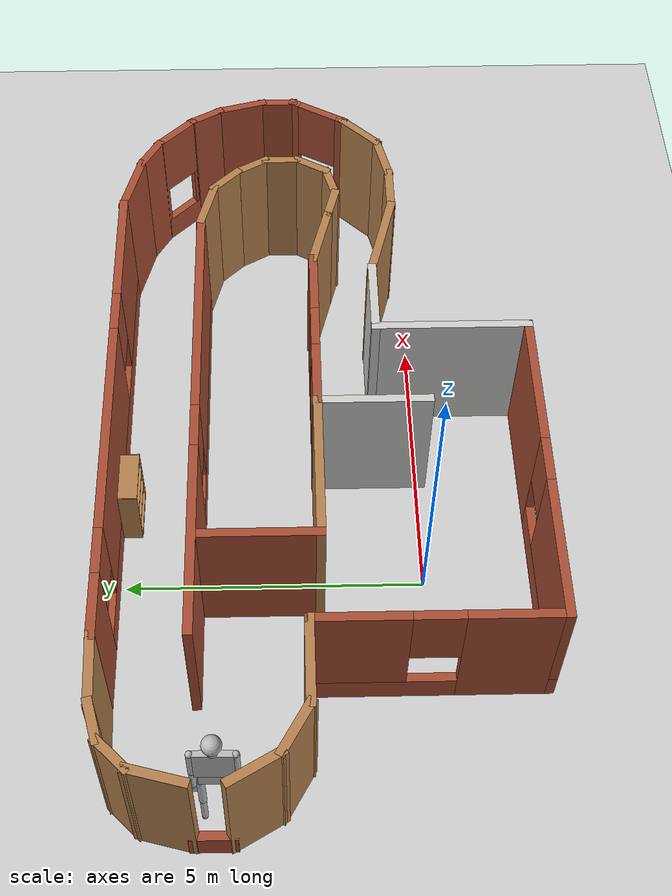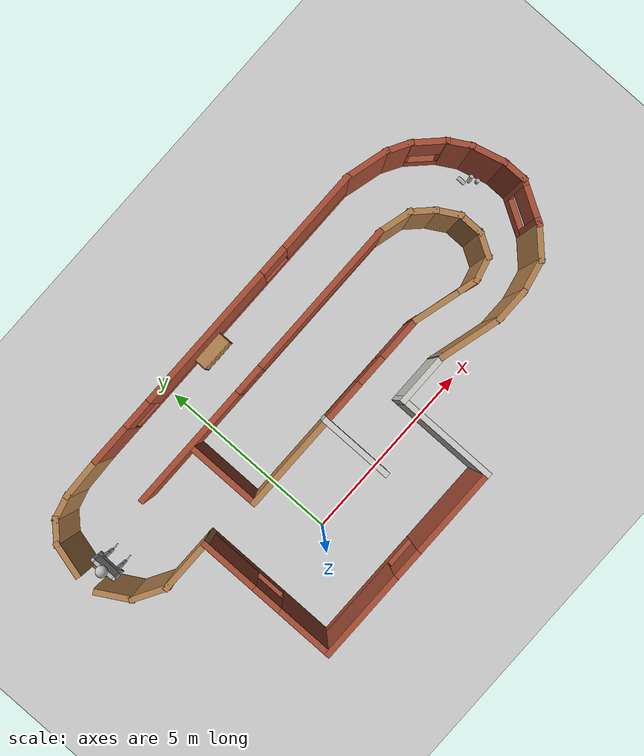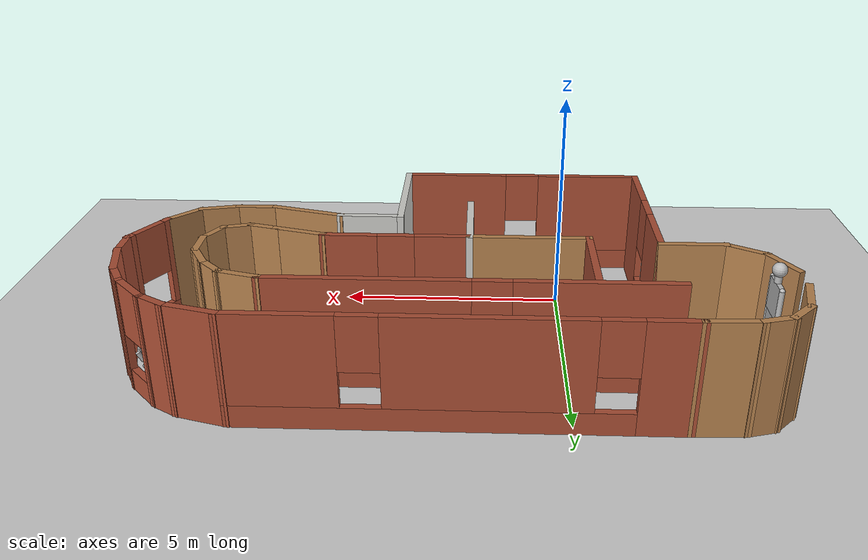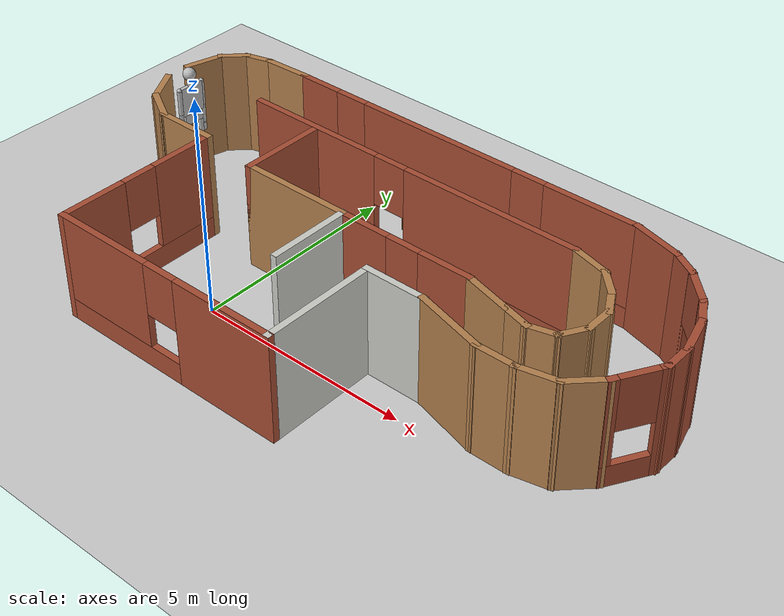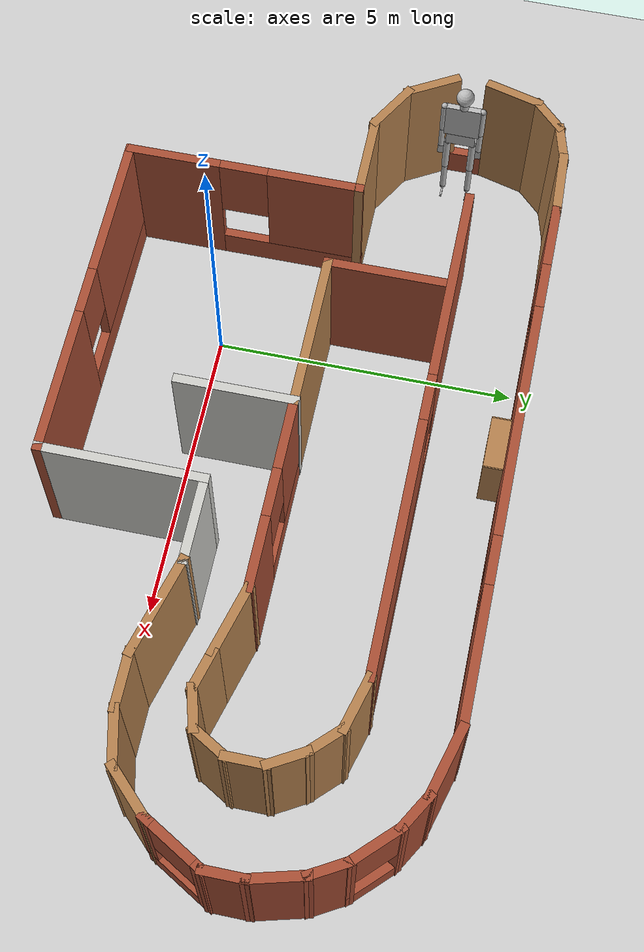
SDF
<sdf version="1.7">
 <world name="default">
  <model name="ground_plane">
   <static>1</static>
   <link name="link">
    <collision name="collision">
     <geometry><plane><normal>0 0 1</normal><size>100 100</size></plane></geometry>
     <surface><friction><ode><mu>100</mu><mu2>50</mu2></ode></friction></surface>
    </collision>
    <visual name="visual">
     <cast_shadows>0</cast_shadows>
     <geometry><plane><normal>0 0 1</normal><size>100 100</size></plane></geometry>
     <material>
      <script><uri>file://media/materials/scripts/gazebo.material</uri><name>Gazebo/Grey</name></script>
     </material>
    </visual>
   </link>
  </model>
  <light name="sun" type="directional">
   <pose>0 0 10 0 -0 0</pose>
   <diffuse>0.8 0.8 0.8 1</diffuse>
   <specular>0.2 0.2 0.2 1</specular>
   <attenuation>
    <range>1000</range>
    <constant>0.9</constant>
    <linear>0.01</linear>
    <quadratic>0.001</quadratic>
   </attenuation>
   <direction>-0.5 0.1 -0.9</direction>
   <spot><inner_angle>0</inner_angle><outer_angle>0</outer_angle><falloff>0</falloff></spot>
  </light>
  <gravity>0 0 -9.8</gravity>
  <magnetic_field>6e-06 2.3e-05 -4.2e-05</magnetic_field>
  <atmosphere type="adiabatic"/>
  <physics type="ode">
   <max_step_size>0.001</max_step_size>
   <real_time_factor>1</real_time_factor>
   <real_time_update_rate>1000</real_time_update_rate>
  </physics>
  <scene><ambient>0.4 0.4 0.4 1</ambient><background>0.7 0.7 0.7 1</background><shadows>1</shadows></scene>
  <spherical_coordinates>
   <surface_model>EARTH_WGS84</surface_model>
   <latitude_deg>0</latitude_deg>
   <longitude_deg>0</longitude_deg>
   <elevation>0</elevation>
   <heading_deg>0</heading_deg>
  </spherical_coordinates>
  <model name="Maze2">
   <pose>2.43404 1.65089 0 0 -0 0</pose>
   <link name="Wall_0">
    <pose>-0.413831 2.09696 0 0 -0 0</pose>
    <visual name="Wall_0_Visual_0">
     <pose>-2.54133 0 1.25 0 -0 0</pose>
     <geometry><box><size>3.41735 0.15 2.5</size></box></geometry>
     <material>
      <script><uri>file://media/materials/scripts/gazebo.material</uri><name>Gazebo/Bricks</name></script>
      <ambient>1 1 1 1</ambient>
     </material>
     <meta><layer>0</layer></meta>
    </visual>
    <collision name="Wall_0_Collision_0">
     <geometry><box><size>3.41735 0.15 2.5</size></box></geometry>
     <pose>-2.54133 0 1.25 0 -0 0</pose>
    </collision>
    <visual name="Wall_0_Visual_1">
     <pose>1.70867 0 0.25 0 -0 0</pose>
     <geometry><box><size>5.08265 0.15 0.5</size></box></geometry>
     <material>
      <script><uri>file://media/materials/scripts/gazebo.material</uri><name>Gazebo/Bricks</name></script>
      <ambient>1 1 1 1</ambient>
     </material>
     <meta><layer>0</layer></meta>
    </visual>
    <collision name="Wall_0_Collision_1">
     <geometry><box><size>5.08265 0.15 0.5</size></box></geometry>
     <pose>1.70867 0 0.25 0 -0 0</pose>
    </collision>
    <visual name="Wall_0_Visual_2">
     <pose>2.10867 0 1.5 0 -0 0</pose>
     <geometry><box><size>4.28265 0.15 2</size></box></geometry>
     <material>
      <script><uri>file://media/materials/scripts/gazebo.material</uri><name>Gazebo/Bricks</name></script>
      <ambient>1 1 1 1</ambient>
     </material>
     <meta><layer>0</layer></meta>
    </visual>
    <collision name="Wall_0_Collision_2">
     <geometry><box><size>4.28265 0.15 2</size></box></geometry>
     <pose>2.10867 0 1.5 0 -0 0</pose>
    </collision>
    <visual name="Wall_0_Visual_3">
     <pose>-0.432651 0 1.9 0 -0 0</pose>
     <geometry><box><size>0.8 0.15 1.2</size></box></geometry>
     <material>
      <script><uri>file://media/materials/scripts/gazebo.material</uri><name>Gazebo/Bricks</name></script>
      <ambient>1 1 1 1</ambient>
     </material>
     <meta><layer>0</layer></meta>
    </visual>
    <collision name="Wall_0_Collision_3">
     <geometry><box><size>0.8 0.15 1.2</size></box></geometry>
     <pose>-0.432651 0 1.9 0 -0 0</pose>
    </collision>
   </link>
   <link name="Wall_1">
    <collision name="Wall_1_Collision">
     <geometry><box><size>1 0.15 2.5</size></box></geometry>
     <pose>0 0 1.25 0 -0 0</pose>
    </collision>
    <visual name="Wall_1_Visual">
     <pose>0 0 1.25 0 -0 0</pose>
     <geometry><box><size>1 0.15 2.5</size></box></geometry>
     <material>
      <script><uri>file://media/materials/scripts/gazebo.material</uri><name>Gazebo/Wood</name></script>
      <ambient>1 1 1 1</ambient>
     </material>
     <meta><layer>0</layer></meta>
    </visual>
    <pose>4.17169 1.98696 0 0 -0 -0.261799</pose>
   </link>
   <link name="Wall_10">
    <collision name="Wall_10_Collision">
     <geometry><box><size>2 0.15 2.5</size></box></geometry>
     <pose>0 0 1.25 0 -0 0</pose>
    </collision>
    <visual name="Wall_10_Visual">
     <pose>0 0 1.25 0 -0 0</pose>
     <geometry><box><size>2 0.15 2.5</size></box></geometry>
     <material>
      <script><uri>file://media/materials/scripts/gazebo.material</uri><name>Gazebo/CeilingTiled</name></script>
      <ambient>1 1 1 1</ambient>
     </material>
     <meta><layer>0</layer></meta>
    </visual>
    <pose>-0.371423 -0.816719 0 0 -0 -1.5708</pose>
   </link>
   <link name="Wall_18">
    <pose>-0.21383 3.51696 0 0 -0 0</pose>
    <visual name="Wall_18_Visual_0">
     <pose>-3.93602 0 1.25 0 -0 0</pose>
     <geometry><box><size>1.12796 0.15 2.5</size></box></geometry>
     <material>
      <script><uri>file://media/materials/scripts/gazebo.material</uri><name>Gazebo/Bricks</name></script>
      <ambient>1 1 1 1</ambient>
     </material>
     <meta><layer>0</layer></meta>
    </visual>
    <collision name="Wall_18_Collision_0">
     <geometry><box><size>1.12796 0.15 2.5</size></box></geometry>
     <pose>-3.93602 0 1.25 0 -0 0</pose>
    </collision>
    <visual name="Wall_18_Visual_1">
     <pose>0.56398 0 0.25 0 -0 0</pose>
     <geometry><box><size>7.87204 0.15 0.5</size></box></geometry>
     <material>
      <script><uri>file://media/materials/scripts/gazebo.material</uri><name>Gazebo/Bricks</name></script>
      <ambient>1 1 1 1</ambient>
     </material>
     <meta><layer>0</layer></meta>
    </visual>
    <collision name="Wall_18_Collision_1">
     <geometry><box><size>7.87204 0.15 0.5</size></box></geometry>
     <pose>0.56398 0 0.25 0 -0 0</pose>
    </collision>
    <visual name="Wall_18_Visual_2">
     <pose>-0.571089 0 1.5 0 -0 0</pose>
     <geometry><box><size>4.0019 0.15 2</size></box></geometry>
     <material>
      <script><uri>file://media/materials/scripts/gazebo.material</uri><name>Gazebo/Bricks</name></script>
      <ambient>1 1 1 1</ambient>
     </material>
     <meta><layer>0</layer></meta>
    </visual>
    <collision name="Wall_18_Collision_2">
     <geometry><box><size>4.0019 0.15 2</size></box></geometry>
     <pose>-0.571089 0 1.5 0 -0 0</pose>
    </collision>
    <visual name="Wall_18_Visual_3">
     <pose>3.36493 0 1.5 0 -0 0</pose>
     <geometry><box><size>2.27014 0.15 2</size></box></geometry>
     <material>
      <script><uri>file://media/materials/scripts/gazebo.material</uri><name>Gazebo/Bricks</name></script>
      <ambient>1 1 1 1</ambient>
     </material>
     <meta><layer>0</layer></meta>
    </visual>
    <collision name="Wall_18_Collision_3">
     <geometry><box><size>2.27014 0.15 2</size></box></geometry>
     <pose>3.36493 0 1.5 0 -0 0</pose>
    </collision>
    <visual name="Wall_18_Visual_4">
     <pose>-2.97204 0 1.9 0 -0 0</pose>
     <geometry><box><size>0.8 0.15 1.2</size></box></geometry>
     <material>
      <script><uri>file://media/materials/scripts/gazebo.material</uri><name>Gazebo/Bricks</name></script>
      <ambient>1 1 1 1</ambient>
     </material>
     <meta><layer>0</layer></meta>
    </visual>
    <collision name="Wall_18_Collision_4">
     <geometry><box><size>0.8 0.15 1.2</size></box></geometry>
     <pose>-2.97204 0 1.9 0 -0 0</pose>
    </collision>
    <visual name="Wall_18_Visual_5">
     <pose>1.82986 0 1.9 0 -0 0</pose>
     <geometry><box><size>0.8 0.15 1.2</size></box></geometry>
     <material>
      <script><uri>file://media/materials/scripts/gazebo.material</uri><name>Gazebo/Bricks</name></script>
      <ambient>1 1 1 1</ambient>
     </material>
     <meta><layer>0</layer></meta>
    </visual>
    <collision name="Wall_18_Collision_5">
     <geometry><box><size>0.8 0.15 1.2</size></box></geometry>
     <pose>1.82986 0 1.9 0 -0 0</pose>
    </collision>
   </link>
   <link name="Wall_19">
    <collision name="Wall_19_Collision">
     <geometry><box><size>1.25 0.15 2.5</size></box></geometry>
     <pose>0 0 1.25 0 -0 0</pose>
    </collision>
    <visual name="Wall_19_Visual">
     <pose>0 0 1.25 0 -0 0</pose>
     <geometry><box><size>1.25 0.15 2.5</size></box></geometry>
     <material>
      <script><uri>file://media/materials/scripts/gazebo.material</uri><name>Gazebo/Bricks</name></script>
      <ambient>1 1 1 1</ambient>
     </material>
     <meta><layer>0</layer></meta>
    </visual>
    <pose>4.74243 3.37461 0 0 -0 -0.261799</pose>
   </link>
   <link name="Wall_2">
    <collision name="Wall_2_Collision">
     <geometry><box><size>0.75 0.15 2.5</size></box></geometry>
     <pose>0 0 1.25 0 -0 0</pose>
    </collision>
    <visual name="Wall_2_Visual">
     <pose>0 0 1.25 0 -0 0</pose>
     <geometry><box><size>0.75 0.15 2.5</size></box></geometry>
     <material>
      <script><uri>file://media/materials/scripts/gazebo.material</uri><name>Gazebo/Wood</name></script>
      <ambient>1 1 1 1</ambient>
     </material>
     <meta><layer>0</layer></meta>
    </visual>
    <pose>4.79434 1.66483 0 0 -0 -0.785398</pose>
   </link>
   <link name="Wall_20">
    <collision name="Wall_20_Collision">
     <geometry><box><size>0.75 0.15 2.5</size></box></geometry>
     <pose>0 0 1.25 0 -0 0</pose>
    </collision>
    <visual name="Wall_20_Visual">
     <pose>0 0 1.25 0 -0 0</pose>
     <geometry><box><size>0.75 0.15 2.5</size></box></geometry>
     <material>
      <script><uri>file://media/materials/scripts/gazebo.material</uri><name>Gazebo/Bricks</name></script>
      <ambient>1 1 1 1</ambient>
     </material>
     <meta><layer>0</layer></meta>
    </visual>
    <pose>5.5335 3.08226 0 0 -0 -0.523599</pose>
   </link>
   <link name="Wall_21">
    <pose>6.09382 2.63174 0 0 -0 -0.785398</pose>
    <visual name="Wall_21_Visual_0">
     <pose>-0.453943 0 1.25 0 -0 0</pose>
     <geometry><box><size>0.092113 0.15 2.5</size></box></geometry>
     <material>
      <script><uri>file://media/materials/scripts/gazebo.material</uri><name>Gazebo/Bricks</name></script>
      <ambient>1 1 1 1</ambient>
     </material>
     <meta><layer>0</layer></meta>
    </visual>
    <collision name="Wall_21_Collision_0">
     <geometry><box><size>0.092113 0.15 2.5</size></box></geometry>
     <pose>-0.453943 0 1.25 0 -0 0</pose>
    </collision>
    <visual name="Wall_21_Visual_1">
     <pose>0.046057 0 0.25 0 -0 0</pose>
     <geometry><box><size>0.907887 0.15 0.5</size></box></geometry>
     <material>
      <script><uri>file://media/materials/scripts/gazebo.material</uri><name>Gazebo/Bricks</name></script>
      <ambient>1 1 1 1</ambient>
     </material>
     <meta><layer>0</layer></meta>
    </visual>
    <collision name="Wall_21_Collision_1">
     <geometry><box><size>0.907887 0.15 0.5</size></box></geometry>
     <pose>0.046057 0 0.25 0 -0 0</pose>
    </collision>
    <visual name="Wall_21_Visual_2">
     <pose>0.446057 0 1.5 0 -0 0</pose>
     <geometry><box><size>0.107887 0.15 2</size></box></geometry>
     <material>
      <script><uri>file://media/materials/scripts/gazebo.material</uri><name>Gazebo/Bricks</name></script>
      <ambient>1 1 1 1</ambient>
     </material>
     <meta><layer>0</layer></meta>
    </visual>
    <collision name="Wall_21_Collision_2">
     <geometry><box><size>0.107887 0.15 2</size></box></geometry>
     <pose>0.446057 0 1.5 0 -0 0</pose>
    </collision>
    <visual name="Wall_21_Visual_3">
     <pose>-0.007887 0 1.9 0 -0 0</pose>
     <geometry><box><size>0.8 0.15 1.2</size></box></geometry>
     <material>
      <script><uri>file://media/materials/scripts/gazebo.material</uri><name>Gazebo/Bricks</name></script>
      <ambient>1 1 1 1</ambient>
     </material>
     <meta><layer>0</layer></meta>
    </visual>
    <collision name="Wall_21_Collision_3">
     <geometry><box><size>0.8 0.15 1.2</size></box></geometry>
     <pose>-0.007887 0 1.9 0 -0 0</pose>
    </collision>
   </link>
   <link name="Wall_22">
    <collision name="Wall_22_Collision">
     <geometry><box><size>0.75 0.15 2.5</size></box></geometry>
     <pose>0 0 1.25 0 -0 0</pose>
    </collision>
    <visual name="Wall_22_Visual">
     <pose>0 0 1.25 0 -0 0</pose>
     <geometry><box><size>0.75 0.15 2.5</size></box></geometry>
     <material>
      <script><uri>file://media/materials/scripts/gazebo.material</uri><name>Gazebo/Bricks</name></script>
      <ambient>1 1 1 1</ambient>
     </material>
     <meta><layer>0</layer></meta>
    </visual>
    <pose>6.54434 2.07141 0 0 -0 -1.0472</pose>
   </link>
   <link name="Wall_23">
    <collision name="Wall_23_Collision">
     <geometry><box><size>1 0.15 2.5</size></box></geometry>
     <pose>0 0 1.25 0 -0 0</pose>
    </collision>
    <visual name="Wall_23_Visual">
     <pose>0 0 1.25 0 -0 0</pose>
     <geometry><box><size>1 0.15 2.5</size></box></geometry>
     <material>
      <script><uri>file://media/materials/scripts/gazebo.material</uri><name>Gazebo/Bricks</name></script>
      <ambient>1 1 1 1</ambient>
     </material>
     <meta><layer>0</layer></meta>
    </visual>
    <pose>6.80434 1.40108 0 0 -0 -1.309</pose>
   </link>
   <link name="Wall_24">
    <collision name="Wall_24_Collision">
     <geometry><box><size>0.75 0.15 2.5</size></box></geometry>
     <pose>0 0 1.25 0 -0 0</pose>
    </collision>
    <visual name="Wall_24_Visual">
     <pose>0 0 1.25 0 -0 0</pose>
     <geometry><box><size>0.75 0.15 2.5</size></box></geometry>
     <material>
      <script><uri>file://media/materials/scripts/gazebo.material</uri><name>Gazebo/Bricks</name></script>
      <ambient>1 1 1 1</ambient>
     </material>
     <meta><layer>0</layer></meta>
    </visual>
    <pose>6.91434 0.690563 0 0 -0 -1.5708</pose>
   </link>
   <link name="Wall_28">
    <pose>6.63934 -0.085751 0 0 -0 -2.0944</pose>
    <visual name="Wall_28_Visual_0">
     <pose>-0.511677 0 1.25 0 -0 0</pose>
     <geometry><box><size>0.226646 0.15 2.5</size></box></geometry>
     <material>
      <script><uri>file://media/materials/scripts/gazebo.material</uri><name>Gazebo/Bricks</name></script>
      <ambient>1 1 1 1</ambient>
     </material>
     <meta><layer>0</layer></meta>
    </visual>
    <collision name="Wall_28_Collision_0">
     <geometry><box><size>0.226646 0.15 2.5</size></box></geometry>
     <pose>-0.511677 0 1.25 0 -0 0</pose>
    </collision>
    <visual name="Wall_28_Visual_1">
     <pose>0.113323 0 0.25 0 -0 0</pose>
     <geometry><box><size>1.02335 0.15 0.5</size></box></geometry>
     <material>
      <script><uri>file://media/materials/scripts/gazebo.material</uri><name>Gazebo/Bricks</name></script>
      <ambient>1 1 1 1</ambient>
     </material>
     <meta><layer>0</layer></meta>
    </visual>
    <collision name="Wall_28_Collision_1">
     <geometry><box><size>1.02335 0.15 0.5</size></box></geometry>
     <pose>0.113323 0 0.25 0 -0 0</pose>
    </collision>
    <visual name="Wall_28_Visual_2">
     <pose>0.513323 0 1.5 0 -0 0</pose>
     <geometry><box><size>0.223354 0.15 2</size></box></geometry>
     <material>
      <script><uri>file://media/materials/scripts/gazebo.material</uri><name>Gazebo/Bricks</name></script>
      <ambient>1 1 1 1</ambient>
     </material>
     <meta><layer>0</layer></meta>
    </visual>
    <collision name="Wall_28_Collision_2">
     <geometry><box><size>0.223354 0.15 2</size></box></geometry>
     <pose>0.513323 0 1.5 0 -0 0</pose>
    </collision>
    <visual name="Wall_28_Visual_3">
     <pose>0.001646 0 1.9 0 -0 0</pose>
     <geometry><box><size>0.8 0.15 1.2</size></box></geometry>
     <material>
      <script><uri>file://media/materials/scripts/gazebo.material</uri><name>Gazebo/Bricks</name></script>
      <ambient>1 1 1 1</ambient>
     </material>
     <meta><layer>0</layer></meta>
    </visual>
    <collision name="Wall_28_Collision_3">
     <geometry><box><size>0.8 0.15 1.2</size></box></geometry>
     <pose>0.001646 0 1.9 0 -0 0</pose>
    </collision>
   </link>
   <link name="Wall_29">
    <collision name="Wall_29_Collision">
     <geometry><box><size>1 0.15 2.5</size></box></geometry>
     <pose>0 0 1.25 0 -0 0</pose>
    </collision>
    <visual name="Wall_29_Visual">
     <pose>0 0 1.25 0 -0 0</pose>
     <geometry><box><size>1 0.15 2.5</size></box></geometry>
     <material>
      <script><uri>file://media/materials/scripts/gazebo.material</uri><name>Gazebo/Wood</name></script>
      <ambient>1 1 1 1</ambient>
     </material>
     <meta><layer>0</layer></meta>
    </visual>
    <pose>6.06382 -0.862585 0 0 -0 -2.35619</pose>
   </link>
   <link name="Wall_3">
    <collision name="Wall_3_Collision">
     <geometry><box><size>0.75 0.15 2.5</size></box></geometry>
     <pose>0 0 1.25 0 -0 0</pose>
    </collision>
    <visual name="Wall_3_Visual">
     <pose>0 0 1.25 0 -0 0</pose>
     <geometry><box><size>0.75 0.15 2.5</size></box></geometry>
     <material>
      <script><uri>file://media/materials/scripts/gazebo.material</uri><name>Gazebo/Wood</name></script>
      <ambient>1 1 1 1</ambient>
     </material>
     <meta><layer>0</layer></meta>
    </visual>
    <pose>5.15647 1.19289 0 0 -0 -1.0472</pose>
   </link>
   <link name="Wall_30">
    <collision name="Wall_30_Collision">
     <geometry><box><size>0.991581 0.15 2.5</size></box></geometry>
     <pose>0 0 1.25 0 -0 0</pose>
    </collision>
    <visual name="Wall_30_Visual">
     <pose>0 0 1.25 0 -0 0</pose>
     <geometry><box><size>0.991581 0.15 2.5</size></box></geometry>
     <material>
      <script><uri>file://media/materials/scripts/gazebo.material</uri><name>Gazebo/Wood</name></script>
      <ambient>1 1 1 1</ambient>
     </material>
     <meta><layer>0</layer></meta>
    </visual>
    <pose>5.35278 -1.25551 0 0 -0 -2.92018</pose>
   </link>
   <link name="Wall_35">
    <collision name="Wall_35_Collision">
     <geometry><box><size>1 0.15 2.5</size></box></geometry>
     <pose>0 0 1.25 0 -0 0</pose>
    </collision>
    <visual name="Wall_35_Visual">
     <pose>0 0 1.25 0 -0 0</pose>
     <geometry><box><size>1 0.15 2.5</size></box></geometry>
     <material>
      <script><uri>file://media/materials/scripts/gazebo.material</uri><name>Gazebo/Wood</name></script>
      <ambient>1 1 1 1</ambient>
     </material>
     <meta><layer>0</layer></meta>
    </visual>
    <pose>4.51726 -1.34792 0 0 -0 3.14159</pose>
   </link>
   <link name="Wall_36">
    <collision name="Wall_36_Collision">
     <geometry><box><size>1.75 0.15 2.5</size></box></geometry>
     <pose>0 0 1.25 0 -0 0</pose>
    </collision>
    <visual name="Wall_36_Visual">
     <pose>0 0 1.25 0 -0 0</pose>
     <geometry><box><size>1.75 0.15 2.5</size></box></geometry>
     <material>
      <script><uri>file://media/materials/scripts/gazebo.material</uri><name>Gazebo/Wood</name></script>
      <ambient>1 1 1 1</ambient>
     </material>
     <meta><layer>0</layer></meta>
    </visual>
    <pose>3.31952 -1.14087 0 0 -0 2.87979</pose>
   </link>
   <link name="Wall_37">
    <collision name="Wall_37_Collision">
     <geometry><box><size>1.5 0.15 2.5</size></box></geometry>
     <pose>0 0 1.25 0 -0 0</pose>
    </collision>
    <visual name="Wall_37_Visual">
     <pose>0 0 1.25 0 -0 0</pose>
     <geometry><box><size>1.5 0.15 2.5</size></box></geometry>
     <material>
      <script><uri>file://media/materials/scripts/gazebo.material</uri><name>Gazebo/CeilingTiled</name></script>
      <ambient>1 1 1 1</ambient>
     </material>
     <meta><layer>0</layer></meta>
    </visual>
    <pose>1.87178 -0.933813 0 0 -0 3.14159</pose>
   </link>
   <link name="Wall_38">
    <collision name="Wall_38_Collision">
     <geometry><box><size>2.75 0.15 2.5</size></box></geometry>
     <pose>0 0 1.25 0 -0 0</pose>
    </collision>
    <visual name="Wall_38_Visual">
     <pose>0 0 1.25 0 -0 0</pose>
     <geometry><box><size>2.75 0.15 2.5</size></box></geometry>
     <material>
      <script><uri>file://media/materials/scripts/gazebo.material</uri><name>Gazebo/CeilingTiled</name></script>
      <ambient>1 1 1 1</ambient>
     </material>
     <meta><layer>0</layer></meta>
    </visual>
    <pose>1.19678 -2.23381 0 0 -0 -1.5708</pose>
   </link>
   <link name="Wall_39">
    <pose>-1.60322 -3.53381 0 0 -0 3.14159</pose>
    <visual name="Wall_39_Visual_0">
     <pose>-1.63033 0 1.25 0 -0 0</pose>
     <geometry><box><size>2.48934 0.15 2.5</size></box></geometry>
     <material>
      <script><uri>file://media/materials/scripts/gazebo.material</uri><name>Gazebo/Bricks</name></script>
      <ambient>1 1 1 1</ambient>
     </material>
     <meta><layer>0</layer></meta>
    </visual>
    <collision name="Wall_39_Collision_0">
     <geometry><box><size>2.48934 0.15 2.5</size></box></geometry>
     <pose>-1.63033 0 1.25 0 -0 0</pose>
    </collision>
    <visual name="Wall_39_Visual_1">
     <pose>1.24467 0 0.25 0 -0 0</pose>
     <geometry><box><size>3.26066 0.15 0.5</size></box></geometry>
     <material>
      <script><uri>file://media/materials/scripts/gazebo.material</uri><name>Gazebo/Bricks</name></script>
      <ambient>1 1 1 1</ambient>
     </material>
     <meta><layer>0</layer></meta>
    </visual>
    <collision name="Wall_39_Collision_1">
     <geometry><box><size>3.26066 0.15 0.5</size></box></geometry>
     <pose>1.24467 0 0.25 0 -0 0</pose>
    </collision>
    <visual name="Wall_39_Visual_2">
     <pose>1.64467 0 1.5 0 -0 0</pose>
     <geometry><box><size>2.46066 0.15 2</size></box></geometry>
     <material>
      <script><uri>file://media/materials/scripts/gazebo.material</uri><name>Gazebo/Bricks</name></script>
      <ambient>1 1 1 1</ambient>
     </material>
     <meta><layer>0</layer></meta>
    </visual>
    <collision name="Wall_39_Collision_2">
     <geometry><box><size>2.46066 0.15 2</size></box></geometry>
     <pose>1.64467 0 1.5 0 -0 0</pose>
    </collision>
    <visual name="Wall_39_Visual_3">
     <pose>0.014341 0 1.9 0 -0 0</pose>
     <geometry><box><size>0.8 0.15 1.2</size></box></geometry>
     <material>
      <script><uri>file://media/materials/scripts/gazebo.material</uri><name>Gazebo/Bricks</name></script>
      <ambient>1 1 1 1</ambient>
     </material>
     <meta><layer>0</layer></meta>
    </visual>
    <collision name="Wall_39_Collision_3">
     <geometry><box><size>0.8 0.15 1.2</size></box></geometry>
     <pose>0.014341 0 1.9 0 -0 0</pose>
    </collision>
   </link>
   <link name="Wall_4">
    <collision name="Wall_4_Collision">
     <geometry><box><size>0.75 0.15 2.5</size></box></geometry>
     <pose>0 0 1.25 0 -0 0</pose>
    </collision>
    <visual name="Wall_4_Visual">
     <pose>0 0 1.25 0 -0 0</pose>
     <geometry><box><size>0.75 0.15 2.5</size></box></geometry>
     <material>
      <script><uri>file://media/materials/scripts/gazebo.material</uri><name>Gazebo/Wood</name></script>
      <ambient>1 1 1 1</ambient>
     </material>
     <meta><layer>0</layer></meta>
    </visual>
    <pose>5.30647 0.633081 0 0 -0 -1.5708</pose>
   </link>
   <link name="Wall_40">
    <pose>-4.40322 -1.60881 0 0 -0 1.5708</pose>
    <visual name="Wall_40_Visual_0">
     <pose>-1.20229 0 1.25 0 -0 0</pose>
     <geometry><box><size>1.59543 0.15 2.5</size></box></geometry>
     <material>
      <script><uri>file://media/materials/scripts/gazebo.material</uri><name>Gazebo/Bricks</name></script>
      <ambient>1 1 1 1</ambient>
     </material>
     <meta><layer>0</layer></meta>
    </visual>
    <collision name="Wall_40_Collision_0">
     <geometry><box><size>1.59543 0.15 2.5</size></box></geometry>
     <pose>-1.20229 0 1.25 0 -0 0</pose>
    </collision>
    <visual name="Wall_40_Visual_1">
     <pose>0.797713 0 0.25 0 -0 0</pose>
     <geometry><box><size>2.40457 0.15 0.5</size></box></geometry>
     <material>
      <script><uri>file://media/materials/scripts/gazebo.material</uri><name>Gazebo/Bricks</name></script>
      <ambient>1 1 1 1</ambient>
     </material>
     <meta><layer>0</layer></meta>
    </visual>
    <collision name="Wall_40_Collision_1">
     <geometry><box><size>2.40457 0.15 0.5</size></box></geometry>
     <pose>0.797713 0 0.25 0 -0 0</pose>
    </collision>
    <visual name="Wall_40_Visual_2">
     <pose>1.19771 0 1.5 0 -0 0</pose>
     <geometry><box><size>1.60457 0.15 2</size></box></geometry>
     <material>
      <script><uri>file://media/materials/scripts/gazebo.material</uri><name>Gazebo/Bricks</name></script>
      <ambient>1 1 1 1</ambient>
     </material>
     <meta><layer>0</layer></meta>
    </visual>
    <collision name="Wall_40_Collision_2">
     <geometry><box><size>1.60457 0.15 2</size></box></geometry>
     <pose>1.19771 0 1.5 0 -0 0</pose>
    </collision>
    <visual name="Wall_40_Visual_3">
     <pose>-0.004573 0 1.9 0 -0 0</pose>
     <geometry><box><size>0.8 0.15 1.2</size></box></geometry>
     <material>
      <script><uri>file://media/materials/scripts/gazebo.material</uri><name>Gazebo/Bricks</name></script>
      <ambient>1 1 1 1</ambient>
     </material>
     <meta><layer>0</layer></meta>
    </visual>
    <collision name="Wall_40_Collision_3">
     <geometry><box><size>0.8 0.15 1.2</size></box></geometry>
     <pose>-0.004573 0 1.9 0 -0 0</pose>
    </collision>
   </link>
   <link name="Wall_42">
    <collision name="Wall_42_Collision">
     <geometry><box><size>2.69392 0.15 2.5</size></box></geometry>
     <pose>0 0 1.25 0 -0 0</pose>
    </collision>
    <visual name="Wall_42_Visual">
     <pose>0 0 1.25 0 -0 0</pose>
     <geometry><box><size>2.69392 0.15 2.5</size></box></geometry>
     <material>
      <script><uri>file://media/materials/scripts/gazebo.material</uri><name>Gazebo/Wood</name></script>
      <ambient>1 1 1 1</ambient>
     </material>
     <meta><layer>0</layer></meta>
    </visual>
    <pose>-1.64329 0.098167 0 0 -0 3.14159</pose>
   </link>
   <link name="Wall_44">
    <collision name="Wall_44_Collision">
     <geometry><box><size>2 0.15 2.5</size></box></geometry>
     <pose>0 0 1.25 0 -0 0</pose>
    </collision>
    <visual name="Wall_44_Visual">
     <pose>0 0 1.25 0 -0 0</pose>
     <geometry><box><size>2 0.15 2.5</size></box></geometry>
     <material>
      <script><uri>file://media/materials/scripts/gazebo.material</uri><name>Gazebo/Bricks</name></script>
      <ambient>1 1 1 1</ambient>
     </material>
     <meta><layer>0</layer></meta>
    </visual>
    <pose>-2.91516 1.02317 0 0 -0 1.5708</pose>
   </link>
   <link name="Wall_46">
    <collision name="Wall_46_Collision">
     <geometry><box><size>1.5 0.15 2.5</size></box></geometry>
     <pose>0 0 1.25 0 -0 0</pose>
    </collision>
    <visual name="Wall_46_Visual">
     <pose>0 0 1.25 0 -0 0</pose>
     <geometry><box><size>1.5 0.15 2.5</size></box></geometry>
     <material>
      <script><uri>file://media/materials/scripts/gazebo.material</uri><name>Gazebo/Wood</name></script>
      <ambient>1 1 1 1</ambient>
     </material>
     <meta><layer>0</layer></meta>
    </visual>
    <pose>-5.07822 0.316187 0 0 -0 3.14159</pose>
   </link>
   <link name="Wall_47">
    <collision name="Wall_47_Collision">
     <geometry><box><size>1 0.15 2.5</size></box></geometry>
     <pose>0 0 1.25 0 -0 0</pose>
    </collision>
    <visual name="Wall_47_Visual">
     <pose>0 0 1.25 0 -0 0</pose>
     <geometry><box><size>1 0.15 2.5</size></box></geometry>
     <material>
      <script><uri>file://media/materials/scripts/gazebo.material</uri><name>Gazebo/Wood</name></script>
      <ambient>1 1 1 1</ambient>
     </material>
     <meta><layer>0</layer></meta>
    </visual>
    <pose>-6.12128 0.528687 0 0 -0 2.61799</pose>
   </link>
   <link name="Wall_48">
    <collision name="Wall_48_Collision">
     <geometry><box><size>1 0.15 2.5</size></box></geometry>
     <pose>0 0 1.25 0 -0 0</pose>
    </collision>
    <visual name="Wall_48_Visual">
     <pose>0 0 1.25 0 -0 0</pose>
     <geometry><box><size>1 0.15 2.5</size></box></geometry>
     <material>
      <script><uri>file://media/materials/scripts/gazebo.material</uri><name>Gazebo/Wood</name></script>
      <ambient>1 1 1 1</ambient>
     </material>
     <meta><layer>0</layer></meta>
    </visual>
    <pose>-6.70184 1.10925 0 0 -0 2.0944</pose>
   </link>
   <link name="Wall_49">
    <pose>-6.91434 1.77731 0 0 -0 1.5708</pose>
    <visual name="Wall_49_Visual_0">
     <pose>0 0 0.25 0 -0 0</pose>
     <geometry><box><size>0.75 0.15 0.5</size></box></geometry>
     <material>
      <script><uri>file://media/materials/scripts/gazebo.material</uri><name>Gazebo/Bricks</name></script>
      <ambient>1 1 1 1</ambient>
     </material>
     <meta><layer>0</layer></meta>
    </visual>
    <collision name="Wall_49_Collision_0">
     <geometry><box><size>0.75 0.15 0.5</size></box></geometry>
     <pose>0 0 0.25 0 -0 0</pose>
    </collision>
   </link>
   <link name="Wall_5">
    <collision name="Wall_5_Collision">
     <geometry><box><size>0.75 0.15 2.5</size></box></geometry>
     <pose>0 0 1.25 0 -0 0</pose>
    </collision>
    <visual name="Wall_5_Visual">
     <pose>0 0 1.25 0 -0 0</pose>
     <geometry><box><size>0.75 0.15 2.5</size></box></geometry>
     <material>
      <script><uri>file://media/materials/scripts/gazebo.material</uri><name>Gazebo/Wood</name></script>
      <ambient>1 1 1 1</ambient>
     </material>
     <meta><layer>0</layer></meta>
    </visual>
    <pose>5.15647 0.073274 0 0 -0 -2.0944</pose>
   </link>
   <link name="Wall_50">
    <collision name="Wall_50_Collision">
     <geometry><box><size>1 0.15 2.5</size></box></geometry>
     <pose>0 0 1.25 0 -0 0</pose>
    </collision>
    <visual name="Wall_50_Visual">
     <pose>0 0 1.25 0 -0 0</pose>
     <geometry><box><size>1 0.15 2.5</size></box></geometry>
     <material>
      <script><uri>file://media/materials/scripts/gazebo.material</uri><name>Gazebo/Wood</name></script>
      <ambient>1 1 1 1</ambient>
     </material>
     <meta><layer>0</layer></meta>
    </visual>
    <pose>-6.80434 2.48783 0 0 -0 1.309</pose>
   </link>
   <link name="Wall_51">
    <collision name="Wall_51_Collision">
     <geometry><box><size>0.75 0.15 2.5</size></box></geometry>
     <pose>0 0 1.25 0 -0 0</pose>
    </collision>
    <visual name="Wall_51_Visual">
     <pose>0 0 1.25 0 -0 0</pose>
     <geometry><box><size>0.75 0.15 2.5</size></box></geometry>
     <material>
      <script><uri>file://media/materials/scripts/gazebo.material</uri><name>Gazebo/Wood</name></script>
      <ambient>1 1 1 1</ambient>
     </material>
     <meta><layer>0</layer></meta>
    </visual>
    <pose>-6.48221 3.11048 0 0 -0 0.785398</pose>
   </link>
   <link name="Wall_52">
    <collision name="Wall_52_Collision">
     <geometry><box><size>0.75 0.15 2.5</size></box></geometry>
     <pose>0 0 1.25 0 -0 0</pose>
    </collision>
    <visual name="Wall_52_Visual">
     <pose>0 0 1.25 0 -0 0</pose>
     <geometry><box><size>0.75 0.15 2.5</size></box></geometry>
     <material>
      <script><uri>file://media/materials/scripts/gazebo.material</uri><name>Gazebo/Wood</name></script>
      <ambient>1 1 1 1</ambient>
     </material>
     <meta><layer>0</layer></meta>
    </visual>
    <pose>-5.9803 3.40026 0 0 -0 0.261799</pose>
   </link>
   <link name="Wall_53">
    <collision name="Wall_53_Collision">
     <geometry><box><size>1.20242 0.15 2.5</size></box></geometry>
     <pose>0 0 1.25 0 -0 0</pose>
    </collision>
    <visual name="Wall_53_Visual">
     <pose>0 0 1.25 0 -0 0</pose>
     <geometry><box><size>1.20242 0.15 2.5</size></box></geometry>
     <material>
      <script><uri>file://media/materials/scripts/gazebo.material</uri><name>Gazebo/Wood</name></script>
      <ambient>1 1 1 1</ambient>
     </material>
     <meta><layer>0</layer></meta>
    </visual>
    <pose>-5.16468 3.49743 0 0 -0 0.037119</pose>
   </link>
   <link name="Wall_6">
    <collision name="Wall_6_Collision">
     <geometry><box><size>0.75 0.15 2.5</size></box></geometry>
     <pose>0 0 1.25 0 -0 0</pose>
    </collision>
    <visual name="Wall_6_Visual">
     <pose>0 0 1.25 0 -0 0</pose>
     <geometry><box><size>0.75 0.15 2.5</size></box></geometry>
     <material>
      <script><uri>file://media/materials/scripts/gazebo.material</uri><name>Gazebo/Wood</name></script>
      <ambient>1 1 1 1</ambient>
     </material>
     <meta><layer>0</layer></meta>
    </visual>
    <pose>4.71669 -0.26418 0 0 -0 -2.87979</pose>
   </link>
   <link name="Wall_7">
    <collision name="Wall_7_Collision">
     <geometry><box><size>0.75 0.15 2.5</size></box></geometry>
     <pose>0 0 1.25 0 -0 0</pose>
    </collision>
    <visual name="Wall_7_Visual">
     <pose>0 0 1.25 0 -0 0</pose>
     <geometry><box><size>0.75 0.15 2.5</size></box></geometry>
     <material>
      <script><uri>file://media/materials/scripts/gazebo.material</uri><name>Gazebo/Wood</name></script>
      <ambient>1 1 1 1</ambient>
     </material>
     <meta><layer>0</layer></meta>
    </visual>
    <pose>4.13714 -0.26418 0 0 -0 2.87979</pose>
   </link>
   <link name="Wall_8">
    <collision name="Wall_8_Collision">
     <geometry><box><size>1.25 0.15 2.5</size></box></geometry>
     <pose>0 0 1.25 0 -0 0</pose>
    </collision>
    <visual name="Wall_8_Visual">
     <pose>0 0 1.25 0 -0 0</pose>
     <geometry><box><size>1.25 0.15 2.5</size></box></geometry>
     <material>
      <script><uri>file://media/materials/scripts/gazebo.material</uri><name>Gazebo/Wood</name></script>
      <ambient>1 1 1 1</ambient>
     </material>
     <meta><layer>0</layer></meta>
    </visual>
    <pose>3.3161 -0.044183 0 0 -0 2.87979</pose>
   </link>
   <link name="Wall_9">
    <pose>1.20671 0.098167 0 0 -0 3.14159</pose>
    <visual name="Wall_9_Visual_0">
     <pose>-1.02934 0 1.25 0 -0 0</pose>
     <geometry><box><size>1.24773 0.15 2.5</size></box></geometry>
     <material>
      <script><uri>file://media/materials/scripts/gazebo.material</uri><name>Gazebo/Bricks</name></script>
      <ambient>1 1 1 1</ambient>
     </material>
     <meta><layer>0</layer></meta>
    </visual>
    <collision name="Wall_9_Collision_0">
     <geometry><box><size>1.24773 0.15 2.5</size></box></geometry>
     <pose>-1.02934 0 1.25 0 -0 0</pose>
    </collision>
    <visual name="Wall_9_Visual_1">
     <pose>0.623864 0 0.25 0 -0 0</pose>
     <geometry><box><size>2.05868 0.15 0.5</size></box></geometry>
     <material>
      <script><uri>file://media/materials/scripts/gazebo.material</uri><name>Gazebo/Bricks</name></script>
      <ambient>1 1 1 1</ambient>
     </material>
     <meta><layer>0</layer></meta>
    </visual>
    <collision name="Wall_9_Collision_1">
     <geometry><box><size>2.05868 0.15 0.5</size></box></geometry>
     <pose>0.623864 0 0.25 0 -0 0</pose>
    </collision>
    <visual name="Wall_9_Visual_2">
     <pose>1.02386 0 1.5 0 -0 0</pose>
     <geometry><box><size>1.25868 0.15 2</size></box></geometry>
     <material>
      <script><uri>file://media/materials/scripts/gazebo.material</uri><name>Gazebo/Bricks</name></script>
      <ambient>1 1 1 1</ambient>
     </material>
     <meta><layer>0</layer></meta>
    </visual>
    <collision name="Wall_9_Collision_2">
     <geometry><box><size>1.25868 0.15 2</size></box></geometry>
     <pose>1.02386 0 1.5 0 -0 0</pose>
    </collision>
    <visual name="Wall_9_Visual_3">
     <pose>-0.005476 0 1.9 0 -0 0</pose>
     <geometry><box><size>0.8 0.15 1.2</size></box></geometry>
     <material>
      <script><uri>file://media/materials/scripts/gazebo.material</uri><name>Gazebo/Bricks</name></script>
      <ambient>1 1 1 1</ambient>
     </material>
     <meta><layer>0</layer></meta>
    </visual>
    <collision name="Wall_9_Collision_3">
     <geometry><box><size>0.8 0.15 1.2</size></box></geometry>
     <pose>-0.005476 0 1.9 0 -0 0</pose>
    </collision>
   </link>
   <static>1</static>
  </model>
  <model name="bookshelf">
   <static>1</static>
   <link name="link">
    <inertial><mass>1</mass></inertial>
    <collision name="back">
     <pose>0 0.005 0.6 0 -0 0</pose>
     <geometry><box><size>0.9 0.01 1.2</size></box></geometry>
    </collision>
    <visual name="visual1">
     <pose>0 0.005 0.6 0 -0 0</pose>
     <geometry><box><size>0.9 0.01 1.2</size></box></geometry>
     <material>
      <script><uri>file://media/materials/scripts/gazebo.material</uri><name>Gazebo/Wood</name></script>
     </material>
    </visual>
    <collision name="left_side">
     <pose>0.45 -0.195 0.6 0 -0 0</pose>
     <geometry><box><size>0.02 0.4 1.2</size></box></geometry>
    </collision>
    <visual name="visual2">
     <pose>0.45 -0.195 0.6 0 -0 0</pose>
     <geometry><box><size>0.02 0.4 1.2</size></box></geometry>
     <material>
      <script><uri>file://media/materials/scripts/gazebo.material</uri><name>Gazebo/Wood</name></script>
     </material>
    </visual>
    <collision name="right_side">
     <pose>-0.45 -0.195 0.6 0 -0 0</pose>
     <geometry><box><size>0.02 0.4 1.2</size></box></geometry>
    </collision>
    <visual name="visual3">
     <pose>-0.45 -0.195 0.6 0 -0 0</pose>
     <geometry><box><size>0.02 0.4 1.2</size></box></geometry>
     <material>
      <script><uri>file://media/materials/scripts/gazebo.material</uri><name>Gazebo/Wood</name></script>
     </material>
    </visual>
    <collision name="bottom">
     <pose>0 -0.195 0.03 0 -0 0</pose>
     <geometry><box><size>0.88 0.4 0.06</size></box></geometry>
    </collision>
    <visual name="visual4">
     <pose>0 -0.195 0.03 0 -0 0</pose>
     <geometry><box><size>0.88 0.4 0.06</size></box></geometry>
     <material>
      <script><uri>file://media/materials/scripts/gazebo.material</uri><name>Gazebo/Wood</name></script>
     </material>
    </visual>
    <collision name="top">
     <pose>0 -0.195 1.19 0 -0 0</pose>
     <geometry><box><size>0.88 0.4 0.02</size></box></geometry>
    </collision>
    <visual name="visual5">
     <pose>0 -0.195 1.19 0 -0 0</pose>
     <geometry><box><size>0.88 0.4 0.02</size></box></geometry>
     <material>
      <script><uri>file://media/materials/scripts/gazebo.material</uri><name>Gazebo/Wood</name></script>
     </material>
    </visual>
    <collision name="low_shelf">
     <pose>0 -0.195 0.43 0 -0 0</pose>
     <geometry><box><size>0.88 0.4 0.02</size></box></geometry>
    </collision>
    <visual name="visual6">
     <pose>0 -0.195 0.43 0 -0 0</pose>
     <geometry><box><size>0.88 0.4 0.02</size></box></geometry>
     <material>
      <script><uri>file://media/materials/scripts/gazebo.material</uri><name>Gazebo/Wood</name></script>
     </material>
    </visual>
    <collision name="high_shelf">
     <pose>0 -0.195 0.8 0 -0 0</pose>
     <geometry><box><size>0.88 0.4 0.02</size></box></geometry>
    </collision>
    <visual name="visual7">
     <pose>0 -0.195 0.8 0 -0 0</pose>
     <geometry><box><size>0.88 0.4 0.02</size></box></geometry>
     <material>
      <script><uri>file://media/materials/scripts/gazebo.material</uri><name>Gazebo/Wood</name></script>
     </material>
    </visual>
   </link>
   <pose>1.48912 5.16105 0 0 -0 0</pose>
  </model>
  <model name="ragdoll">
   <pose>-4.00735 3.35612 1.4 -2e-06 -0.000948 -0.011685</pose>
   <link name="hip">
    <inertial>
     <inertia><ixx>0.1</ixx><ixy>0</ixy><ixz>0</ixz><iyy>0.1</iyy><iyz>0</iyz><izz>0.1</izz></inertia>
     <mass>10</mass>
    </inertial>
    <collision name="hip_geom">
     <pose>0 0 0.125 0 -0 0</pose>
     <geometry><box><size>0.1 0.5 0.25</size></box></geometry>
     <surface>
      <friction><ode><mu>-1</mu><mu2>-1</mu2><fdir1>0 0 0</fdir1><slip1>0</slip1><slip2>0</slip2></ode></friction>
      <bounce><restitution_coefficient>0</restitution_coefficient><threshold>100000</threshold></bounce>
      <contact>
       <ode>
        <soft_cfm>0</soft_cfm>
        <soft_erp>0.2</soft_erp>
        <kp>1e+12</kp>
        <kd>1</kd>
        <max_vel>0</max_vel>
        <min_depth>0.001</min_depth>
       </ode>
      </contact>
     </surface>
    </collision>
    <visual name="hip_geom_visual">
     <pose>0 0 0.125 0 -0 0</pose>
     <geometry><box><size>0.1 0.5 0.25</size></box></geometry>
    </visual>
    <gravity>0</gravity>
   </link>
   <link name="l_thigh_pan">
    <pose>0 0.22 0 0 -0 0</pose>
    <inertial>
     <inertia><ixx>0.01</ixx><ixy>0</ixy><ixz>0</ixz><iyy>0.01</iyy><iyz>0</iyz><izz>0.01</izz></inertia>
     <mass>1</mass>
    </inertial>
    <collision name="l_thigh_pan_geom">
     <pose>0 0 -0.03 0 -0 0</pose>
     <geometry><sphere><radius>0.06</radius></sphere></geometry>
     <surface>
      <friction><ode><mu>-1</mu><mu2>-1</mu2><fdir1>0 0 0</fdir1><slip1>0</slip1><slip2>0</slip2></ode></friction>
      <bounce><restitution_coefficient>0</restitution_coefficient><threshold>100000</threshold></bounce>
      <contact>
       <ode>
        <soft_cfm>0</soft_cfm>
        <soft_erp>0.2</soft_erp>
        <kp>1e+12</kp>
        <kd>1</kd>
        <max_vel>0</max_vel>
        <min_depth>0.001</min_depth>
       </ode>
      </contact>
     </surface>
    </collision>
    <visual name="l_thigh_pan_geom_visual">
     <pose>0 0 -0.03 0 -0 0</pose>
     <geometry><sphere><radius>0.06</radius></sphere></geometry>
    </visual>
    <gravity>0</gravity>
   </link>
   <link name="l_thigh_lift">
    <pose>0 0.22 0 0 -0 0</pose>
    <inertial>
     <inertia><ixx>0.05</ixx><ixy>0</ixy><ixz>0</ixz><iyy>0.05</iyy><iyz>0</iyz><izz>0.05</izz></inertia>
     <mass>5</mass>
    </inertial>
    <collision name="l_thigh_lift_geom">
     <pose>0 0 -0.35 0 -0 0</pose>
     <geometry><cylinder><radius>0.06</radius><length>0.7</length></cylinder></geometry>
     <surface>
      <friction><ode><mu>-1</mu><mu2>-1</mu2><fdir1>0 0 0</fdir1><slip1>0</slip1><slip2>0</slip2></ode></friction>
      <bounce><restitution_coefficient>0</restitution_coefficient><threshold>100000</threshold></bounce>
      <contact>
       <ode>
        <soft_cfm>0</soft_cfm>
        <soft_erp>0.2</soft_erp>
        <kp>1e+12</kp>
        <kd>1</kd>
        <max_vel>0</max_vel>
        <min_depth>0.001</min_depth>
       </ode>
      </contact>
     </surface>
    </collision>
    <visual name="l_thigh_lift_geom_visual">
     <pose>0 0 -0.35 0 -0 0</pose>
     <geometry><cylinder><radius>0.06</radius><length>0.7</length></cylinder></geometry>
    </visual>
    <gravity>0</gravity>
   </link>
   <link name="l_calf">
    <pose>0 0.22 -0.7 0 -0 0</pose>
    <inertial>
     <inertia><ixx>0.02</ixx><ixy>0</ixy><ixz>0</ixz><iyy>0.02</iyy><iyz>0</iyz><izz>0.02</izz></inertia>
     <mass>2</mass>
    </inertial>
    <collision name="l_calf_geom">
     <pose>0 0 -0.3 0 -0 0</pose>
     <geometry><cylinder><radius>0.05</radius><length>0.6</length></cylinder></geometry>
     <surface>
      <friction><ode><mu>-1</mu><mu2>-1</mu2><fdir1>0 0 0</fdir1><slip1>0</slip1><slip2>0</slip2></ode></friction>
      <bounce><restitution_coefficient>0</restitution_coefficient><threshold>100000</threshold></bounce>
      <contact>
       <ode>
        <soft_cfm>0</soft_cfm>
        <soft_erp>0.2</soft_erp>
        <kp>1e+12</kp>
        <kd>1</kd>
        <max_vel>0</max_vel>
        <min_depth>0.001</min_depth>
       </ode>
      </contact>
     </surface>
    </collision>
    <visual name="l_calf_geom_visual">
     <pose>0 0 -0.3 0 -0 0</pose>
     <geometry><cylinder><radius>0.05</radius><length>0.6</length></cylinder></geometry>
    </visual>
    <gravity>0</gravity>
   </link>
   <link name="l_ankle">
    <pose>0 0.22 -1.325 0 -0 0</pose>
    <inertial>
     <inertia><ixx>0.01</ixx><ixy>0</ixy><ixz>0</ixz><iyy>0.01</iyy><iyz>0</iyz><izz>0.01</izz></inertia>
     <mass>1</mass>
    </inertial>
    <collision name="l_ankle_geom">
     <geometry><sphere><radius>0.05</radius></sphere></geometry>
     <surface>
      <friction><ode><mu>-1</mu><mu2>-1</mu2><fdir1>0 0 0</fdir1><slip1>0</slip1><slip2>0</slip2></ode></friction>
      <bounce><restitution_coefficient>0</restitution_coefficient><threshold>100000</threshold></bounce>
      <contact>
       <ode>
        <soft_cfm>0</soft_cfm>
        <soft_erp>0.2</soft_erp>
        <kp>1e+12</kp>
        <kd>1</kd>
        <max_vel>0</max_vel>
        <min_depth>0.001</min_depth>
       </ode>
      </contact>
     </surface>
    </collision>
    <visual name="l_ankle_geom_visual"><geometry><sphere><radius>0.05</radius></sphere></geometry></visual>
    <gravity>0</gravity>
   </link>
   <link name="l_foot">
    <pose>0 0.22 -1.35 0 -0 0</pose>
    <inertial>
     <pose>0.1 0 0 0 -0 0</pose>
     <inertia><ixx>0.01</ixx><ixy>0</ixy><ixz>0</ixz><iyy>0.01</iyy><iyz>0</iyz><izz>0.01</izz></inertia>
     <mass>1</mass>
    </inertial>
    <collision name="l_foot_geom">
     <pose>0.1 0 -0.025 0 -0 0</pose>
     <geometry><box><size>0.2 0.03 0.05</size></box></geometry>
     <surface>
      <friction><ode><mu>-1</mu><mu2>-1</mu2><fdir1>0 0 0</fdir1><slip1>0</slip1><slip2>0</slip2></ode></friction>
      <bounce><restitution_coefficient>0</restitution_coefficient><threshold>100000</threshold></bounce>
      <contact>
       <ode>
        <soft_cfm>0</soft_cfm>
        <soft_erp>0.2</soft_erp>
        <kp>1e+12</kp>
        <kd>1</kd>
        <max_vel>0</max_vel>
        <min_depth>0.001</min_depth>
       </ode>
      </contact>
     </surface>
    </collision>
    <visual name="l_foot_geom_visual">
     <pose>0.1 0 -0.025 0 -0 0</pose>
     <geometry><box><size>0.2 0.03 0.05</size></box></geometry>
    </visual>
   </link>
   <link name="r_thigh_pan">
    <pose>0 -0.22 0 0 -0 0</pose>
    <inertial>
     <inertia><ixx>0.01</ixx><ixy>0</ixy><ixz>0</ixz><iyy>0.01</iyy><iyz>0</iyz><izz>0.01</izz></inertia>
     <mass>1</mass>
    </inertial>
    <collision name="r_thigh_pan_geom">
     <pose>0 0 -0.03 0 -0 0</pose>
     <geometry><sphere><radius>0.06</radius></sphere></geometry>
     <surface>
      <friction><ode><mu>-1</mu><mu2>-1</mu2><fdir1>0 0 0</fdir1><slip1>0</slip1><slip2>0</slip2></ode></friction>
      <bounce><restitution_coefficient>0</restitution_coefficient><threshold>100000</threshold></bounce>
      <contact>
       <ode>
        <soft_cfm>0</soft_cfm>
        <soft_erp>0.2</soft_erp>
        <kp>1e+12</kp>
        <kd>1</kd>
        <max_vel>0</max_vel>
        <min_depth>0.001</min_depth>
       </ode>
      </contact>
     </surface>
    </collision>
    <visual name="r_thigh_pan_geom_visual">
     <pose>0 0 -0.03 0 -0 0</pose>
     <geometry><sphere><radius>0.06</radius></sphere></geometry>
    </visual>
    <gravity>0</gravity>
   </link>
   <link name="r_thigh_lift">
    <pose>0 -0.22 0 0 -0 0</pose>
    <inertial>
     <inertia><ixx>0.05</ixx><ixy>0</ixy><ixz>0</ixz><iyy>0.05</iyy><iyz>0</iyz><izz>0.05</izz></inertia>
     <mass>5</mass>
    </inertial>
    <collision name="r_thigh_lift_geom">
     <pose>0 0 -0.35 0 -0 0</pose>
     <geometry><cylinder><radius>0.06</radius><length>0.7</length></cylinder></geometry>
     <surface>
      <friction><ode><mu>-1</mu><mu2>-1</mu2><fdir1>0 0 0</fdir1><slip1>0</slip1><slip2>0</slip2></ode></friction>
      <bounce><restitution_coefficient>0</restitution_coefficient><threshold>100000</threshold></bounce>
      <contact>
       <ode>
        <soft_cfm>0</soft_cfm>
        <soft_erp>0.2</soft_erp>
        <kp>1e+12</kp>
        <kd>1</kd>
        <max_vel>0</max_vel>
        <min_depth>0.001</min_depth>
       </ode>
      </contact>
     </surface>
    </collision>
    <visual name="r_thigh_lift_geom_visual">
     <pose>0 0 -0.35 0 -0 0</pose>
     <geometry><cylinder><radius>0.06</radius><length>0.7</length></cylinder></geometry>
    </visual>
    <gravity>0</gravity>
   </link>
   <link name="r_calf">
    <pose>0 -0.22 -0.7 0 -0 0</pose>
    <inertial>
     <inertia><ixx>0.02</ixx><ixy>0</ixy><ixz>0</ixz><iyy>0.02</iyy><iyz>0</iyz><izz>0.02</izz></inertia>
     <mass>2</mass>
    </inertial>
    <collision name="r_calf_geom">
     <pose>0 0 -0.3 0 -0 0</pose>
     <geometry><cylinder><radius>0.05</radius><length>0.6</length></cylinder></geometry>
     <surface>
      <friction><ode><mu>-1</mu><mu2>-1</mu2><fdir1>0 0 0</fdir1><slip1>0</slip1><slip2>0</slip2></ode></friction>
      <bounce><restitution_coefficient>0</restitution_coefficient><threshold>100000</threshold></bounce>
      <contact>
       <ode>
        <soft_cfm>0</soft_cfm>
        <soft_erp>0.2</soft_erp>
        <kp>1e+12</kp>
        <kd>1</kd>
        <max_vel>0</max_vel>
        <min_depth>0.001</min_depth>
       </ode>
      </contact>
     </surface>
    </collision>
    <visual name="r_calf_geom_visual">
     <pose>0 0 -0.3 0 -0 0</pose>
     <geometry><cylinder><radius>0.05</radius><length>0.6</length></cylinder></geometry>
    </visual>
    <gravity>0</gravity>
   </link>
   <link name="r_ankle">
    <pose>0 -0.22 -1.325 0 -0 0</pose>
    <inertial>
     <inertia><ixx>0.01</ixx><ixy>0</ixy><ixz>0</ixz><iyy>0.01</iyy><iyz>0</iyz><izz>0.01</izz></inertia>
     <mass>1</mass>
    </inertial>
    <collision name="r_ankle_geom">
     <geometry><sphere><radius>0.05</radius></sphere></geometry>
     <surface>
      <friction><ode><mu>-1</mu><mu2>-1</mu2><fdir1>0 0 0</fdir1><slip1>0</slip1><slip2>0</slip2></ode></friction>
      <bounce><restitution_coefficient>0</restitution_coefficient><threshold>100000</threshold></bounce>
      <contact>
       <ode>
        <soft_cfm>0</soft_cfm>
        <soft_erp>0.2</soft_erp>
        <kp>1e+12</kp>
        <kd>1</kd>
        <max_vel>0</max_vel>
        <min_depth>0.001</min_depth>
       </ode>
      </contact>
     </surface>
    </collision>
    <visual name="r_ankle_geom_visual"><geometry><sphere><radius>0.05</radius></sphere></geometry></visual>
    <gravity>0</gravity>
   </link>
   <link name="r_foot">
    <pose>0 -0.22 -1.35 0 -0 0</pose>
    <inertial>
     <pose>0.1 0 0 0 -0 0</pose>
     <inertia><ixx>0.01</ixx><ixy>0</ixy><ixz>0</ixz><iyy>0.01</iyy><iyz>0</iyz><izz>0.01</izz></inertia>
     <mass>1</mass>
    </inertial>
    <collision name="r_foot_geom">
     <pose>0.1 0 -0.025 0 -0 0</pose>
     <geometry><box><size>0.2 0.03 0.05</size></box></geometry>
     <surface>
      <friction><ode><mu>-1</mu><mu2>-1</mu2><fdir1>0 0 0</fdir1><slip1>0</slip1><slip2>0</slip2></ode></friction>
      <bounce><restitution_coefficient>0</restitution_coefficient><threshold>100000</threshold></bounce>
      <contact>
       <ode>
        <soft_cfm>0</soft_cfm>
        <soft_erp>0.2</soft_erp>
        <kp>1e+12</kp>
        <kd>1</kd>
        <max_vel>0</max_vel>
        <min_depth>0.001</min_depth>
       </ode>
      </contact>
     </surface>
    </collision>
    <visual name="r_foot_geom_visual">
     <pose>0.1 0 -0.025 0 -0 0</pose>
     <geometry><box><size>0.2 0.03 0.05</size></box></geometry>
    </visual>
   </link>
   <link name="torso">
    <pose>0 0 0.25 0 -0 0</pose>
    <inertial>
     <inertia><ixx>0.3</ixx><ixy>0</ixy><ixz>0</ixz><iyy>0.3</iyy><iyz>0</iyz><izz>0.3</izz></inertia>
     <mass>30</mass>
    </inertial>
    <collision name="torso_geom">
     <pose>0 0 0.35 0 -0 0</pose>
     <geometry><box><size>0.1 0.6 0.7</size></box></geometry>
     <surface>
      <friction><ode><mu>-1</mu><mu2>-1</mu2><fdir1>0 0 0</fdir1><slip1>0</slip1><slip2>0</slip2></ode></friction>
      <bounce><restitution_coefficient>0</restitution_coefficient><threshold>100000</threshold></bounce>
      <contact>
       <ode>
        <soft_cfm>0</soft_cfm>
        <soft_erp>0.2</soft_erp>
        <kp>1e+12</kp>
        <kd>1</kd>
        <max_vel>0</max_vel>
        <min_depth>0.001</min_depth>
       </ode>
      </contact>
     </surface>
    </collision>
    <visual name="torso_geom_visual">
     <pose>0 0 0.35 0 -0 0</pose>
     <geometry><box><size>0.1 0.6 0.7</size></box></geometry>
    </visual>
    <gravity>0</gravity>
   </link>
   <link name="l_shoulder">
    <pose>0 0.3275 0.9225 0 -0 0</pose>
    <inertial>
     <inertia><ixx>0.01</ixx><ixy>0</ixy><ixz>0</ixz><iyy>0.01</iyy><iyz>0</iyz><izz>0.01</izz></inertia>
     <mass>1</mass>
    </inertial>
    <collision name="l_shoulder_geom">
     <geometry><sphere><radius>0.055</radius></sphere></geometry>
     <surface>
      <friction><ode><mu>-1</mu><mu2>-1</mu2><fdir1>0 0 0</fdir1><slip1>0</slip1><slip2>0</slip2></ode></friction>
      <bounce><restitution_coefficient>0</restitution_coefficient><threshold>100000</threshold></bounce>
      <contact>
       <ode>
        <soft_cfm>0</soft_cfm>
        <soft_erp>0.2</soft_erp>
        <kp>1e+12</kp>
        <kd>1</kd>
        <max_vel>0</max_vel>
        <min_depth>0.001</min_depth>
       </ode>
      </contact>
     </surface>
    </collision>
    <visual name="l_shoulder_geom_visual"><geometry><sphere><radius>0.055</radius></sphere></geometry></visual>
    <gravity>0</gravity>
   </link>
   <link name="l_upper_arm">
    <pose>0 0.3275 0.9225 0 -0 0</pose>
    <inertial>
     <inertia><ixx>0.02</ixx><ixy>0</ixy><ixz>0</ixz><iyy>0.02</iyy><iyz>0</iyz><izz>0.02</izz></inertia>
     <mass>2</mass>
    </inertial>
    <collision name="l_upper_arm_geom">
     <pose>0 0 -0.3 0 -0 0</pose>
     <geometry><cylinder><radius>0.055</radius><length>0.6</length></cylinder></geometry>
     <surface>
      <friction><ode><mu>-1</mu><mu2>-1</mu2><fdir1>0 0 0</fdir1><slip1>0</slip1><slip2>0</slip2></ode></friction>
      <bounce><restitution_coefficient>0</restitution_coefficient><threshold>100000</threshold></bounce>
      <contact>
       <ode>
        <soft_cfm>0</soft_cfm>
        <soft_erp>0.2</soft_erp>
        <kp>1e+12</kp>
        <kd>1</kd>
        <max_vel>0</max_vel>
        <min_depth>0.001</min_depth>
       </ode>
      </contact>
     </surface>
    </collision>
    <visual name="l_upper_arm_geom_visual">
     <pose>0 0 -0.3 0 -0 0</pose>
     <geometry><cylinder><radius>0.055</radius><length>0.6</length></cylinder></geometry>
    </visual>
    <gravity>0</gravity>
   </link>
   <link name="l_forearm">
    <pose>0 0.3275 0.3225 0 -0 0</pose>
    <inertial>
     <inertia><ixx>0.01</ixx><ixy>0</ixy><ixz>0</ixz><iyy>0.01</iyy><iyz>0</iyz><izz>0.01</izz></inertia>
     <mass>1</mass>
    </inertial>
    <collision name="l_forearm_geom">
     <pose>0 0 -0.225 0 -0 0</pose>
     <geometry><cylinder><radius>0.05</radius><length>0.45</length></cylinder></geometry>
     <surface>
      <friction><ode><mu>-1</mu><mu2>-1</mu2><fdir1>0 0 0</fdir1><slip1>0</slip1><slip2>0</slip2></ode></friction>
      <bounce><restitution_coefficient>0</restitution_coefficient><threshold>100000</threshold></bounce>
      <contact>
       <ode>
        <soft_cfm>0</soft_cfm>
        <soft_erp>0.2</soft_erp>
        <kp>1e+12</kp>
        <kd>1</kd>
        <max_vel>0</max_vel>
        <min_depth>0.001</min_depth>
       </ode>
      </contact>
     </surface>
    </collision>
    <visual name="l_forearm_geom_visual">
     <pose>0 0 -0.225 0 -0 0</pose>
     <geometry><cylinder><radius>0.05</radius><length>0.45</length></cylinder></geometry>
    </visual>
    <gravity>0</gravity>
   </link>
   <link name="l_wrist">
    <pose>0 0.3275 -0.1425 0 -0 0</pose>
    <inertial>
     <inertia><ixx>0.01</ixx><ixy>0</ixy><ixz>0</ixz><iyy>0.01</iyy><iyz>0</iyz><izz>0.01</izz></inertia>
     <mass>1</mass>
    </inertial>
    <collision name="l_wrist_geom">
     <geometry><sphere><radius>0.03</radius></sphere></geometry>
     <surface>
      <friction><ode><mu>-1</mu><mu2>-1</mu2><fdir1>0 0 0</fdir1><slip1>0</slip1><slip2>0</slip2></ode></friction>
      <bounce><restitution_coefficient>0</restitution_coefficient><threshold>100000</threshold></bounce>
      <contact>
       <ode>
        <soft_cfm>0</soft_cfm>
        <soft_erp>0.2</soft_erp>
        <kp>1e+12</kp>
        <kd>1</kd>
        <max_vel>0</max_vel>
        <min_depth>0.001</min_depth>
       </ode>
      </contact>
     </surface>
    </collision>
    <visual name="l_wrist_geom_visual"><geometry><sphere><radius>0.03</radius></sphere></geometry></visual>
    <gravity>0</gravity>
   </link>
   <link name="l_hand">
    <pose>0 0.3275 -0.1575 0 -0 0</pose>
    <inertial>
     <inertia><ixx>0.01</ixx><ixy>0</ixy><ixz>0</ixz><iyy>0.01</iyy><iyz>0</iyz><izz>0.01</izz></inertia>
     <mass>1</mass>
    </inertial>
    <collision name="l_hand_geom">
     <pose>0 0 -0.1 0 -0 0</pose>
     <geometry><box><size>0.03 0.1 0.2</size></box></geometry>
     <surface>
      <friction><ode><mu>-1</mu><mu2>-1</mu2><fdir1>0 0 0</fdir1><slip1>0</slip1><slip2>0</slip2></ode></friction>
      <bounce><restitution_coefficient>0</restitution_coefficient><threshold>100000</threshold></bounce>
      <contact>
       <ode>
        <soft_cfm>0</soft_cfm>
        <soft_erp>0.2</soft_erp>
        <kp>1e+12</kp>
        <kd>1</kd>
        <max_vel>0</max_vel>
        <min_depth>0.001</min_depth>
       </ode>
      </contact>
     </surface>
    </collision>
    <visual name="l_hand_geom_visual">
     <pose>0 0 -0.1 0 -0 0</pose>
     <geometry><box><size>0.03 0.1 0.2</size></box></geometry>
    </visual>
    <gravity>0</gravity>
   </link>
   <link name="neck">
    <pose>0 0 0.95 0 -0 0</pose>
    <inertial>
     <inertia><ixx>0.01</ixx><ixy>0</ixy><ixz>0</ixz><iyy>0.01</iyy><iyz>0</iyz><izz>0.01</izz></inertia>
     <mass>1</mass>
    </inertial>
    <collision name="neck_geom">
     <pose>0 0 0.1 0 -0 0</pose>
     <geometry><cylinder><radius>0.075</radius><length>0.2</length></cylinder></geometry>
     <surface>
      <friction><ode><mu>-1</mu><mu2>-1</mu2><fdir1>0 0 0</fdir1><slip1>0</slip1><slip2>0</slip2></ode></friction>
      <bounce><restitution_coefficient>0</restitution_coefficient><threshold>100000</threshold></bounce>
      <contact>
       <ode>
        <soft_cfm>0</soft_cfm>
        <soft_erp>0.2</soft_erp>
        <kp>1e+12</kp>
        <kd>1</kd>
        <max_vel>0</max_vel>
        <min_depth>0.001</min_depth>
       </ode>
      </contact>
     </surface>
    </collision>
    <visual name="neck_geom_visual">
     <pose>0 0 0.1 0 -0 0</pose>
     <geometry><cylinder><radius>0.075</radius><length>0.2</length></cylinder></geometry>
    </visual>
    <gravity>0</gravity>
   </link>
   <link name="head">
    <pose>0 0 1.225 0 -0 0</pose>
    <inertial>
     <inertia><ixx>0.1</ixx><ixy>0</ixy><ixz>0</ixz><iyy>0.1</iyy><iyz>0</iyz><izz>0.1</izz></inertia>
     <mass>10</mass>
    </inertial>
    <collision name="head_geom">
     <geometry><sphere><radius>0.15</radius></sphere></geometry>
     <surface>
      <friction><ode><mu>-1</mu><mu2>-1</mu2><fdir1>0 0 0</fdir1><slip1>0</slip1><slip2>0</slip2></ode></friction>
      <bounce><restitution_coefficient>0</restitution_coefficient><threshold>100000</threshold></bounce>
      <contact>
       <ode>
        <soft_cfm>0</soft_cfm>
        <soft_erp>0.2</soft_erp>
        <kp>1e+12</kp>
        <kd>1</kd>
        <max_vel>0</max_vel>
        <min_depth>0.001</min_depth>
       </ode>
      </contact>
     </surface>
    </collision>
    <visual name="head_geom_visual"><geometry><sphere><radius>0.15</radius></sphere></geometry></visual>
    <gravity>0</gravity>
   </link>
   <link name="r_shoulder">
    <pose>0 -0.3275 0.9225 0 -0 0</pose>
    <inertial>
     <inertia><ixx>0.01</ixx><ixy>0</ixy><ixz>0</ixz><iyy>0.01</iyy><iyz>0</iyz><izz>0.01</izz></inertia>
     <mass>1</mass>
    </inertial>
    <collision name="r_shoulder_geom">
     <geometry><sphere><radius>0.055</radius></sphere></geometry>
     <surface>
      <friction><ode><mu>-1</mu><mu2>-1</mu2><fdir1>0 0 0</fdir1><slip1>0</slip1><slip2>0</slip2></ode></friction>
      <bounce><restitution_coefficient>0</restitution_coefficient><threshold>100000</threshold></bounce>
      <contact>
       <ode>
        <soft_cfm>0</soft_cfm>
        <soft_erp>0.2</soft_erp>
        <kp>1e+12</kp>
        <kd>1</kd>
        <max_vel>0</max_vel>
        <min_depth>0.001</min_depth>
       </ode>
      </contact>
     </surface>
    </collision>
    <visual name="r_shoulder_geom_visual"><geometry><sphere><radius>0.055</radius></sphere></geometry></visual>
    <gravity>0</gravity>
   </link>
   <link name="r_upper_arm">
    <pose>0 -0.3275 0.9225 0 -0 0</pose>
    <inertial>
     <inertia><ixx>0.02</ixx><ixy>0</ixy><ixz>0</ixz><iyy>0.02</iyy><iyz>0</iyz><izz>0.02</izz></inertia>
     <mass>2</mass>
    </inertial>
    <collision name="r_upper_arm_geom">
     <pose>0 0 -0.3 0 -0 0</pose>
     <geometry><cylinder><radius>0.055</radius><length>0.6</length></cylinder></geometry>
     <surface>
      <friction><ode><mu>-1</mu><mu2>-1</mu2><fdir1>0 0 0</fdir1><slip1>0</slip1><slip2>0</slip2></ode></friction>
      <bounce><restitution_coefficient>0</restitution_coefficient><threshold>100000</threshold></bounce>
      <contact>
       <ode>
        <soft_cfm>0</soft_cfm>
        <soft_erp>0.2</soft_erp>
        <kp>1e+12</kp>
        <kd>1</kd>
        <max_vel>0</max_vel>
        <min_depth>0.001</min_depth>
       </ode>
      </contact>
     </surface>
    </collision>
    <visual name="r_upper_arm_geom_visual">
     <pose>0 0 -0.3 0 -0 0</pose>
     <geometry><cylinder><radius>0.055</radius><length>0.6</length></cylinder></geometry>
    </visual>
    <gravity>0</gravity>
   </link>
   <link name="r_forearm">
    <pose>0 -0.3275 0.3225 0 -0 0</pose>
    <inertial>
     <inertia><ixx>0.01</ixx><ixy>0</ixy><ixz>0</ixz><iyy>0.01</iyy><iyz>0</iyz><izz>0.01</izz></inertia>
     <mass>1</mass>
    </inertial>
    <collision name="r_forearm_geom">
     <pose>0 0 -0.225 0 -0 0</pose>
     <geometry><cylinder><radius>0.05</radius><length>0.45</length></cylinder></geometry>
     <surface>
      <friction><ode><mu>-1</mu><mu2>-1</mu2><fdir1>0 0 0</fdir1><slip1>0</slip1><slip2>0</slip2></ode></friction>
      <bounce><restitution_coefficient>0</restitution_coefficient><threshold>100000</threshold></bounce>
      <contact>
       <ode>
        <soft_cfm>0</soft_cfm>
        <soft_erp>0.2</soft_erp>
        <kp>1e+12</kp>
        <kd>1</kd>
        <max_vel>0</max_vel>
        <min_depth>0.001</min_depth>
       </ode>
      </contact>
     </surface>
    </collision>
    <visual name="r_forearm_geom_visual">
     <pose>0 0 -0.225 0 -0 0</pose>
     <geometry><cylinder><radius>0.05</radius><length>0.45</length></cylinder></geometry>
    </visual>
    <gravity>0</gravity>
   </link>
   <link name="r_wrist">
    <pose>0 -0.3275 -0.1425 0 -0 0</pose>
    <inertial>
     <inertia><ixx>0.01</ixx><ixy>0</ixy><ixz>0</ixz><iyy>0.01</iyy><iyz>0</iyz><izz>0.01</izz></inertia>
     <mass>1</mass>
    </inertial>
    <collision name="r_wrist_geom">
     <geometry><sphere><radius>0.03</radius></sphere></geometry>
     <surface>
      <friction><ode><mu>-1</mu><mu2>-1</mu2><fdir1>0 0 0</fdir1><slip1>0</slip1><slip2>0</slip2></ode></friction>
      <bounce><restitution_coefficient>0</restitution_coefficient><threshold>100000</threshold></bounce>
      <contact>
       <ode>
        <soft_cfm>0</soft_cfm>
        <soft_erp>0.2</soft_erp>
        <kp>1e+12</kp>
        <kd>1</kd>
        <max_vel>0</max_vel>
        <min_depth>0.001</min_depth>
       </ode>
      </contact>
     </surface>
    </collision>
    <visual name="r_wrist_geom_visual"><geometry><sphere><radius>0.03</radius></sphere></geometry></visual>
    <gravity>0</gravity>
   </link>
   <link name="r_hand">
    <pose>0 -0.3275 -0.1575 0 -0 0</pose>
    <inertial>
     <inertia><ixx>0.01</ixx><ixy>0</ixy><ixz>0</ixz><iyy>0.01</iyy><iyz>0</iyz><izz>0.01</izz></inertia>
     <mass>1</mass>
    </inertial>
    <collision name="r_hand_geom">
     <pose>0 0 -0.1 0 -0 0</pose>
     <geometry><box><size>0.03 0.1 0.2</size></box></geometry>
     <surface>
      <friction><ode><mu>-1</mu><mu2>-1</mu2><fdir1>0 0 0</fdir1><slip1>0</slip1><slip2>0</slip2></ode></friction>
      <bounce><restitution_coefficient>0</restitution_coefficient><threshold>100000</threshold></bounce>
      <contact>
       <ode>
        <soft_cfm>0</soft_cfm>
        <soft_erp>0.2</soft_erp>
        <kp>1e+12</kp>
        <kd>1</kd>
        <max_vel>0</max_vel>
        <min_depth>0.001</min_depth>
       </ode>
      </contact>
     </surface>
    </collision>
    <visual name="r_hand_geom_visual">
     <pose>0 0 -0.1 0 -0 0</pose>
     <geometry><box><size>0.03 0.1 0.2</size></box></geometry>
    </visual>
    <gravity>0</gravity>
   </link>
   <joint name="l_thigh_pan_joint" type="revolute">
    <parent>hip</parent>
    <child>l_thigh_pan</child>
    <axis>
     <dynamics>
      <damping>0</damping>
      <friction>0</friction>
      <spring_reference>0</spring_reference>
      <spring_stiffness>0</spring_stiffness>
     </dynamics>
     <limit><lower>-1.5708</lower><upper>1.5708</upper><effort>0</effort><velocity>0</velocity></limit>
     <xyz expressed_in="__model__">0 0 1</xyz>
    </axis>
   </joint>
   <joint name="l_thigh_lift_joint" type="revolute">
    <parent>l_thigh_pan</parent>
    <child>l_thigh_lift</child>
    <axis>
     <dynamics>
      <damping>0</damping>
      <friction>0</friction>
      <spring_reference>0</spring_reference>
      <spring_stiffness>0</spring_stiffness>
     </dynamics>
     <limit><lower>-1.5708</lower><upper>1.5708</upper><effort>0</effort><velocity>0</velocity></limit>
     <xyz expressed_in="__model__">0 1 0</xyz>
    </axis>
   </joint>
   <joint name="l_calf_joint" type="revolute">
    <parent>l_thigh_lift</parent>
    <child>l_calf</child>
    <axis>
     <dynamics>
      <damping>0</damping>
      <friction>0</friction>
      <spring_reference>0</spring_reference>
      <spring_stiffness>0</spring_stiffness>
     </dynamics>
     <limit><lower>-1.5708</lower><upper>1.5708</upper><effort>0</effort><velocity>0</velocity></limit>
     <xyz expressed_in="__model__">0 1 0</xyz>
    </axis>
   </joint>
   <joint name="l_ankle_joint" type="revolute">
    <parent>l_calf</parent>
    <child>l_ankle</child>
    <axis>
     <dynamics>
      <damping>0</damping>
      <friction>0</friction>
      <spring_reference>0</spring_reference>
      <spring_stiffness>0</spring_stiffness>
     </dynamics>
     <limit><lower>-1.5708</lower><upper>1.5708</upper><effort>0</effort><velocity>0</velocity></limit>
     <xyz expressed_in="__model__">0 1 0</xyz>
    </axis>
   </joint>
   <joint name="l_foot_joint" type="revolute">
    <parent>l_ankle</parent>
    <child>l_foot</child>
    <axis>
     <dynamics>
      <damping>0</damping>
      <friction>0</friction>
      <spring_reference>0</spring_reference>
      <spring_stiffness>0</spring_stiffness>
     </dynamics>
     <limit><lower>-1.5708</lower><upper>1.5708</upper><effort>0</effort><velocity>0</velocity></limit>
     <xyz expressed_in="__model__">1 0 0</xyz>
    </axis>
   </joint>
   <joint name="r_thigh_pan_joint" type="revolute">
    <parent>hip</parent>
    <child>r_thigh_pan</child>
    <axis>
     <dynamics>
      <damping>0</damping>
      <friction>0</friction>
      <spring_reference>0</spring_reference>
      <spring_stiffness>0</spring_stiffness>
     </dynamics>
     <limit><lower>-1.5708</lower><upper>1.5708</upper><effort>0</effort><velocity>0</velocity></limit>
     <xyz expressed_in="__model__">0 0 1</xyz>
    </axis>
   </joint>
   <joint name="r_thigh_lift_joint" type="revolute">
    <parent>r_thigh_pan</parent>
    <child>r_thigh_lift</child>
    <axis>
     <dynamics>
      <damping>0</damping>
      <friction>0</friction>
      <spring_reference>0</spring_reference>
      <spring_stiffness>0</spring_stiffness>
     </dynamics>
     <limit><lower>-1.5708</lower><upper>1.5708</upper><effort>0</effort><velocity>0</velocity></limit>
     <xyz expressed_in="__model__">0 1 0</xyz>
    </axis>
   </joint>
   <joint name="r_calf_joint" type="revolute">
    <parent>r_thigh_lift</parent>
    <child>r_calf</child>
    <axis>
     <dynamics>
      <damping>0</damping>
      <friction>0</friction>
      <spring_reference>0</spring_reference>
      <spring_stiffness>0</spring_stiffness>
     </dynamics>
     <limit><lower>-1.5708</lower><upper>1.5708</upper><effort>0</effort><velocity>0</velocity></limit>
     <xyz expressed_in="__model__">0 1 0</xyz>
    </axis>
   </joint>
   <joint name="r_ankle_joint" type="revolute">
    <parent>r_calf</parent>
    <child>r_ankle</child>
    <axis>
     <dynamics>
      <damping>0</damping>
      <friction>0</friction>
      <spring_reference>0</spring_reference>
      <spring_stiffness>0</spring_stiffness>
     </dynamics>
     <limit><lower>-1.5708</lower><upper>1.5708</upper><effort>0</effort><velocity>0</velocity></limit>
     <xyz expressed_in="__model__">0 1 0</xyz>
    </axis>
   </joint>
   <joint name="r_foot_joint" type="revolute">
    <parent>r_ankle</parent>
    <child>r_foot</child>
    <axis>
     <dynamics>
      <damping>0</damping>
      <friction>0</friction>
      <spring_reference>0</spring_reference>
      <spring_stiffness>0</spring_stiffness>
     </dynamics>
     <limit><lower>-1.5708</lower><upper>1.5708</upper><effort>0</effort><velocity>0</velocity></limit>
     <xyz expressed_in="__model__">1 0 0</xyz>
    </axis>
   </joint>
   <joint name="torso_joint" type="revolute">
    <parent>hip</parent>
    <child>torso</child>
    <axis>
     <dynamics>
      <damping>0</damping>
      <friction>0</friction>
      <spring_reference>0</spring_reference>
      <spring_stiffness>0</spring_stiffness>
     </dynamics>
     <limit><lower>-1.5708</lower><upper>1.5708</upper><effort>0</effort><velocity>0</velocity></limit>
     <xyz expressed_in="__model__">0 1 0</xyz>
    </axis>
   </joint>
   <joint name="l_shoulder_joint" type="revolute">
    <parent>torso</parent>
    <child>l_shoulder</child>
    <axis>
     <dynamics>
      <damping>0</damping>
      <friction>0</friction>
      <spring_reference>0</spring_reference>
      <spring_stiffness>0</spring_stiffness>
     </dynamics>
     <limit><lower>-1.5708</lower><upper>1.5708</upper><effort>0</effort><velocity>0</velocity></limit>
     <xyz expressed_in="__model__">1 0 0</xyz>
    </axis>
   </joint>
   <joint name="l_upper_arm_joint" type="revolute">
    <parent>l_shoulder</parent>
    <child>l_upper_arm</child>
    <axis>
     <dynamics>
      <damping>0</damping>
      <friction>0</friction>
      <spring_reference>0</spring_reference>
      <spring_stiffness>0</spring_stiffness>
     </dynamics>
     <limit><lower>-1.5708</lower><upper>1.5708</upper><effort>0</effort><velocity>0</velocity></limit>
     <xyz expressed_in="__model__">0 1 0</xyz>
    </axis>
   </joint>
   <joint name="l_forearm_joint" type="revolute">
    <parent>l_upper_arm</parent>
    <child>l_forearm</child>
    <axis>
     <dynamics>
      <damping>0</damping>
      <friction>0</friction>
      <spring_reference>0</spring_reference>
      <spring_stiffness>0</spring_stiffness>
     </dynamics>
     <limit><lower>-1.5708</lower><upper>1.5708</upper><effort>0</effort><velocity>0</velocity></limit>
     <xyz expressed_in="__model__">0 1 0</xyz>
    </axis>
   </joint>
   <joint name="l_wrist_joint" type="revolute">
    <parent>l_forearm</parent>
    <child>l_wrist</child>
    <axis>
     <dynamics>
      <damping>0</damping>
      <friction>0</friction>
      <spring_reference>0</spring_reference>
      <spring_stiffness>0</spring_stiffness>
     </dynamics>
     <limit><lower>-1.5708</lower><upper>1.5708</upper><effort>0</effort><velocity>0</velocity></limit>
     <xyz expressed_in="__model__">0 1 0</xyz>
    </axis>
   </joint>
   <joint name="l_hand_joint" type="revolute">
    <parent>l_wrist</parent>
    <child>l_hand</child>
    <axis>
     <dynamics>
      <damping>0</damping>
      <friction>0</friction>
      <spring_reference>0</spring_reference>
      <spring_stiffness>0</spring_stiffness>
     </dynamics>
     <limit><lower>-1.5708</lower><upper>1.5708</upper><effort>0</effort><velocity>0</velocity></limit>
     <xyz expressed_in="__model__">0 1 0</xyz>
    </axis>
   </joint>
   <joint name="neck_joint" type="revolute">
    <parent>torso</parent>
    <child>neck</child>
    <axis>
     <dynamics>
      <damping>0</damping>
      <friction>0</friction>
      <spring_reference>0</spring_reference>
      <spring_stiffness>0</spring_stiffness>
     </dynamics>
     <limit><lower>-1.5708</lower><upper>1.5708</upper><effort>0</effort><velocity>0</velocity></limit>
     <xyz expressed_in="__model__">0 0 1</xyz>
    </axis>
   </joint>
   <joint name="head_joint" type="revolute">
    <parent>neck</parent>
    <child>head</child>
    <axis>
     <dynamics>
      <damping>0</damping>
      <friction>0</friction>
      <spring_reference>0</spring_reference>
      <spring_stiffness>0</spring_stiffness>
     </dynamics>
     <limit><lower>-1.5708</lower><upper>1.5708</upper><effort>0</effort><velocity>0</velocity></limit>
     <xyz expressed_in="__model__">0 1 0</xyz>
    </axis>
   </joint>
   <joint name="r_shoulder_joint" type="revolute">
    <parent>torso</parent>
    <child>r_shoulder</child>
    <axis>
     <dynamics>
      <damping>0</damping>
      <friction>0</friction>
      <spring_reference>0</spring_reference>
      <spring_stiffness>0</spring_stiffness>
     </dynamics>
     <limit><lower>-1.5708</lower><upper>1.5708</upper><effort>0</effort><velocity>0</velocity></limit>
     <xyz expressed_in="__model__">1 0 0</xyz>
    </axis>
   </joint>
   <joint name="r_upper_arm_joint" type="revolute">
    <parent>r_shoulder</parent>
    <child>r_upper_arm</child>
    <axis>
     <dynamics>
      <damping>0</damping>
      <friction>0</friction>
      <spring_reference>0</spring_reference>
      <spring_stiffness>0</spring_stiffness>
     </dynamics>
     <limit><lower>-1.5708</lower><upper>1.5708</upper><effort>0</effort><velocity>0</velocity></limit>
     <xyz expressed_in="__model__">0 1 0</xyz>
    </axis>
   </joint>
   <joint name="r_forearm_joint" type="revolute">
    <parent>r_upper_arm</parent>
    <child>r_forearm</child>
    <axis>
     <dynamics>
      <damping>0</damping>
      <friction>0</friction>
      <spring_reference>0</spring_reference>
      <spring_stiffness>0</spring_stiffness>
     </dynamics>
     <limit><lower>-1.5708</lower><upper>1.5708</upper><effort>0</effort><velocity>0</velocity></limit>
     <xyz expressed_in="__model__">0 1 0</xyz>
    </axis>
   </joint>
   <joint name="r_wrist_joint" type="revolute">
    <parent>r_forearm</parent>
    <child>r_wrist</child>
    <axis>
     <dynamics>
      <damping>0</damping>
      <friction>0</friction>
      <spring_reference>0</spring_reference>
      <spring_stiffness>0</spring_stiffness>
     </dynamics>
     <limit><lower>-1.5708</lower><upper>1.5708</upper><effort>0</effort><velocity>0</velocity></limit>
     <xyz expressed_in="__model__">0 1 0</xyz>
    </axis>
   </joint>
   <joint name="r_hand_joint" type="revolute">
    <parent>r_wrist</parent>
    <child>r_hand</child>
    <axis>
     <dynamics>
      <damping>0</damping>
      <friction>0</friction>
      <spring_reference>0</spring_reference>
      <spring_stiffness>0</spring_stiffness>
     </dynamics>
     <limit><lower>-1.5708</lower><upper>1.5708</upper><effort>0</effort><velocity>0</velocity></limit>
     <xyz expressed_in="__model__">0 1 0</xyz>
    </axis>
   </joint>
   <static>0</static>
  </model>
  <model name="beer">
   <link name="link">
    <pose>0 0 0.115 0 -0 0</pose>
    <inertial>
     <mass>0.39</mass>
     <inertia><ixx>0.00058</ixx><ixy>0</ixy><ixz>0</ixz><iyy>0.00058</iyy><iyz>0</iyz><izz>0.00019</izz></inertia>
    </inertial>
    <collision name="collision">
     <geometry><cylinder><radius>0.055</radius><length>0.23</length></cylinder></geometry>
    </collision>
    <visual name="visual">
     <geometry><cylinder><radius>0.055</radius><length>0.23</length></cylinder></geometry>
     <material>
      <script>
       <uri>model://beer/materials/scripts</uri>
       <uri>model://beer/materials/textures</uri>
       <name>Beer/Diffuse</name>
      </script>
     </material>
    </visual>
   </link>
   <pose>9.01616 3.00433 0.024583 -0.178479 0.429948 -0.123402</pose>
  </model>
  <model name="beer_0">
   <link name="link">
    <pose>0 0 0.115 0 -0 0</pose>
    <inertial>
     <mass>0.39</mass>
     <inertia><ixx>0.00058</ixx><ixy>0</ixy><ixz>0</ixz><iyy>0.00058</iyy><iyz>0</iyz><izz>0.00019</izz></inertia>
    </inertial>
    <collision name="collision">
     <geometry><cylinder><radius>0.055</radius><length>0.23</length></cylinder></geometry>
    </collision>
    <visual name="visual">
     <geometry><cylinder><radius>0.055</radius><length>0.23</length></cylinder></geometry>
     <material>
      <script>
       <uri>model://beer/materials/scripts</uri>
       <uri>model://beer/materials/textures</uri>
       <name>Beer/Diffuse</name>
      </script>
     </material>
    </visual>
   </link>
   <pose>9.1419 2.83996 -2e-06 1e-06 -0 -1e-06</pose>
  </model>
  <model name="beer_1">
   <link name="link">
    <pose>0 0 0.115 0 -0 0</pose>
    <inertial>
     <mass>0.39</mass>
     <inertia><ixx>0.00058</ixx><ixy>0</ixy><ixz>0</ixz><iyy>0.00058</iyy><iyz>0</iyz><izz>0.00019</izz></inertia>
    </inertial>
    <collision name="collision">
     <geometry><cylinder><radius>0.055</radius><length>0.23</length></cylinder></geometry>
    </collision>
    <visual name="visual">
     <geometry><cylinder><radius>0.055</radius><length>0.23</length></cylinder></geometry>
     <material>
      <script>
       <uri>model://beer/materials/scripts</uri>
       <uri>model://beer/materials/textures</uri>
       <name>Beer/Diffuse</name>
      </script>
     </material>
    </visual>
   </link>
   <pose>8.896 3.27012 0.055 1.57115 -0 0</pose>
  </model>
 </world>
</sdf>
